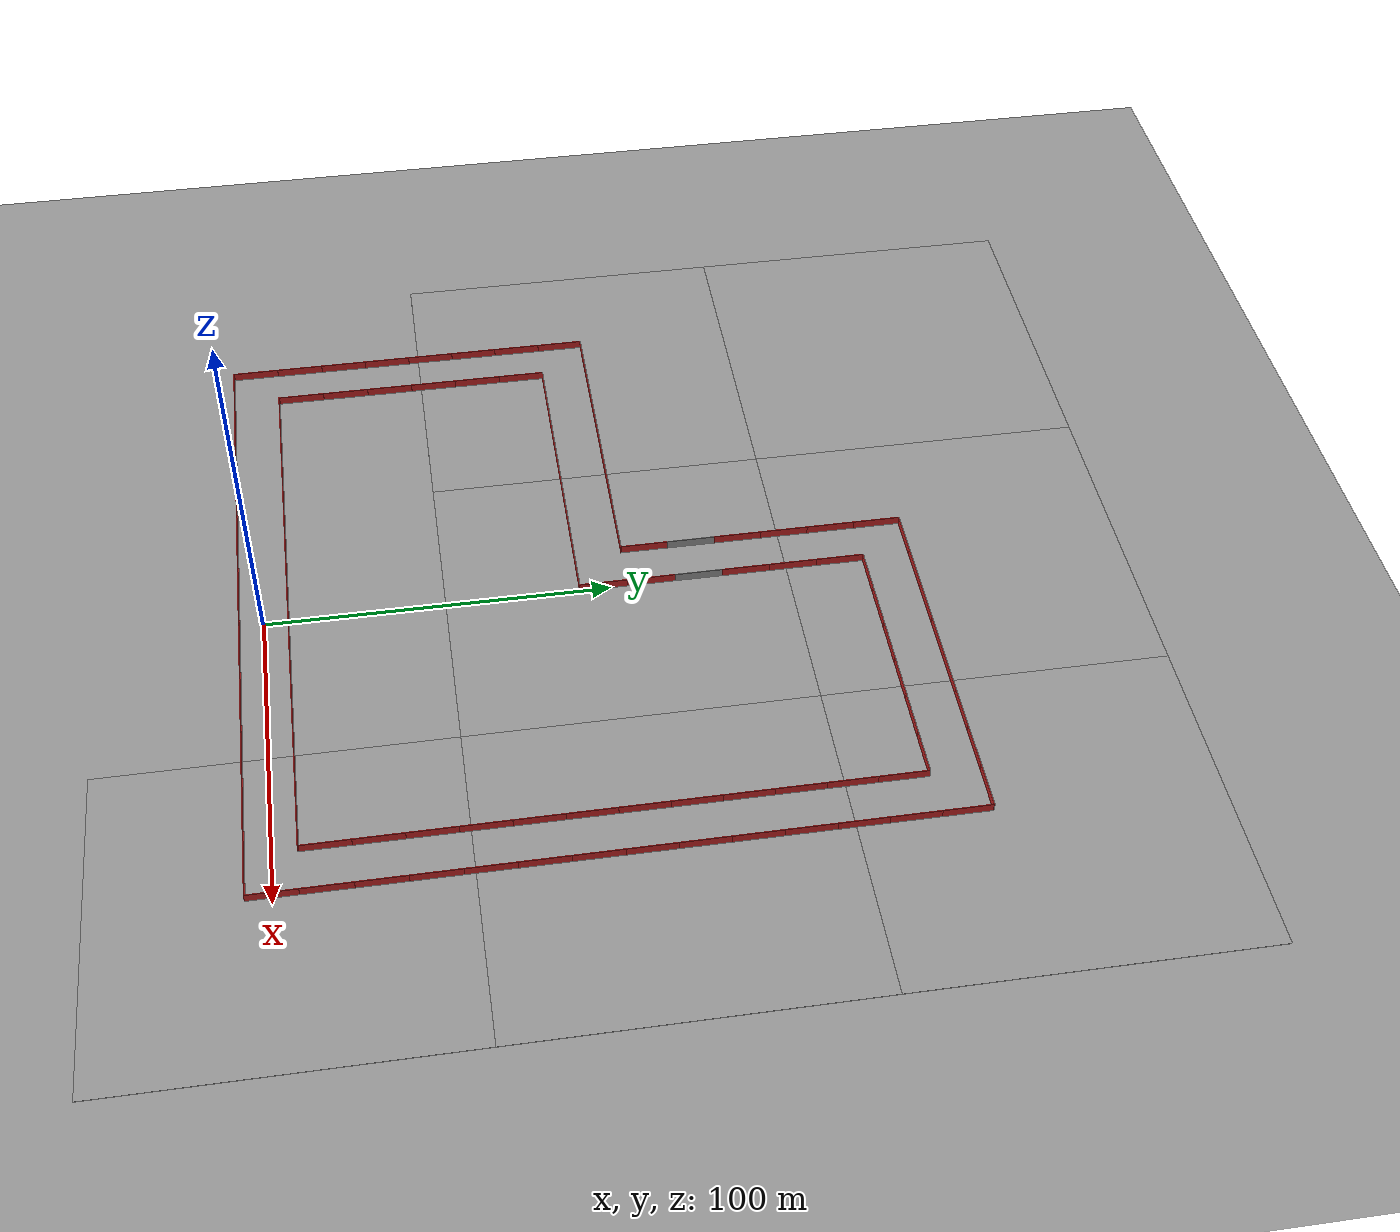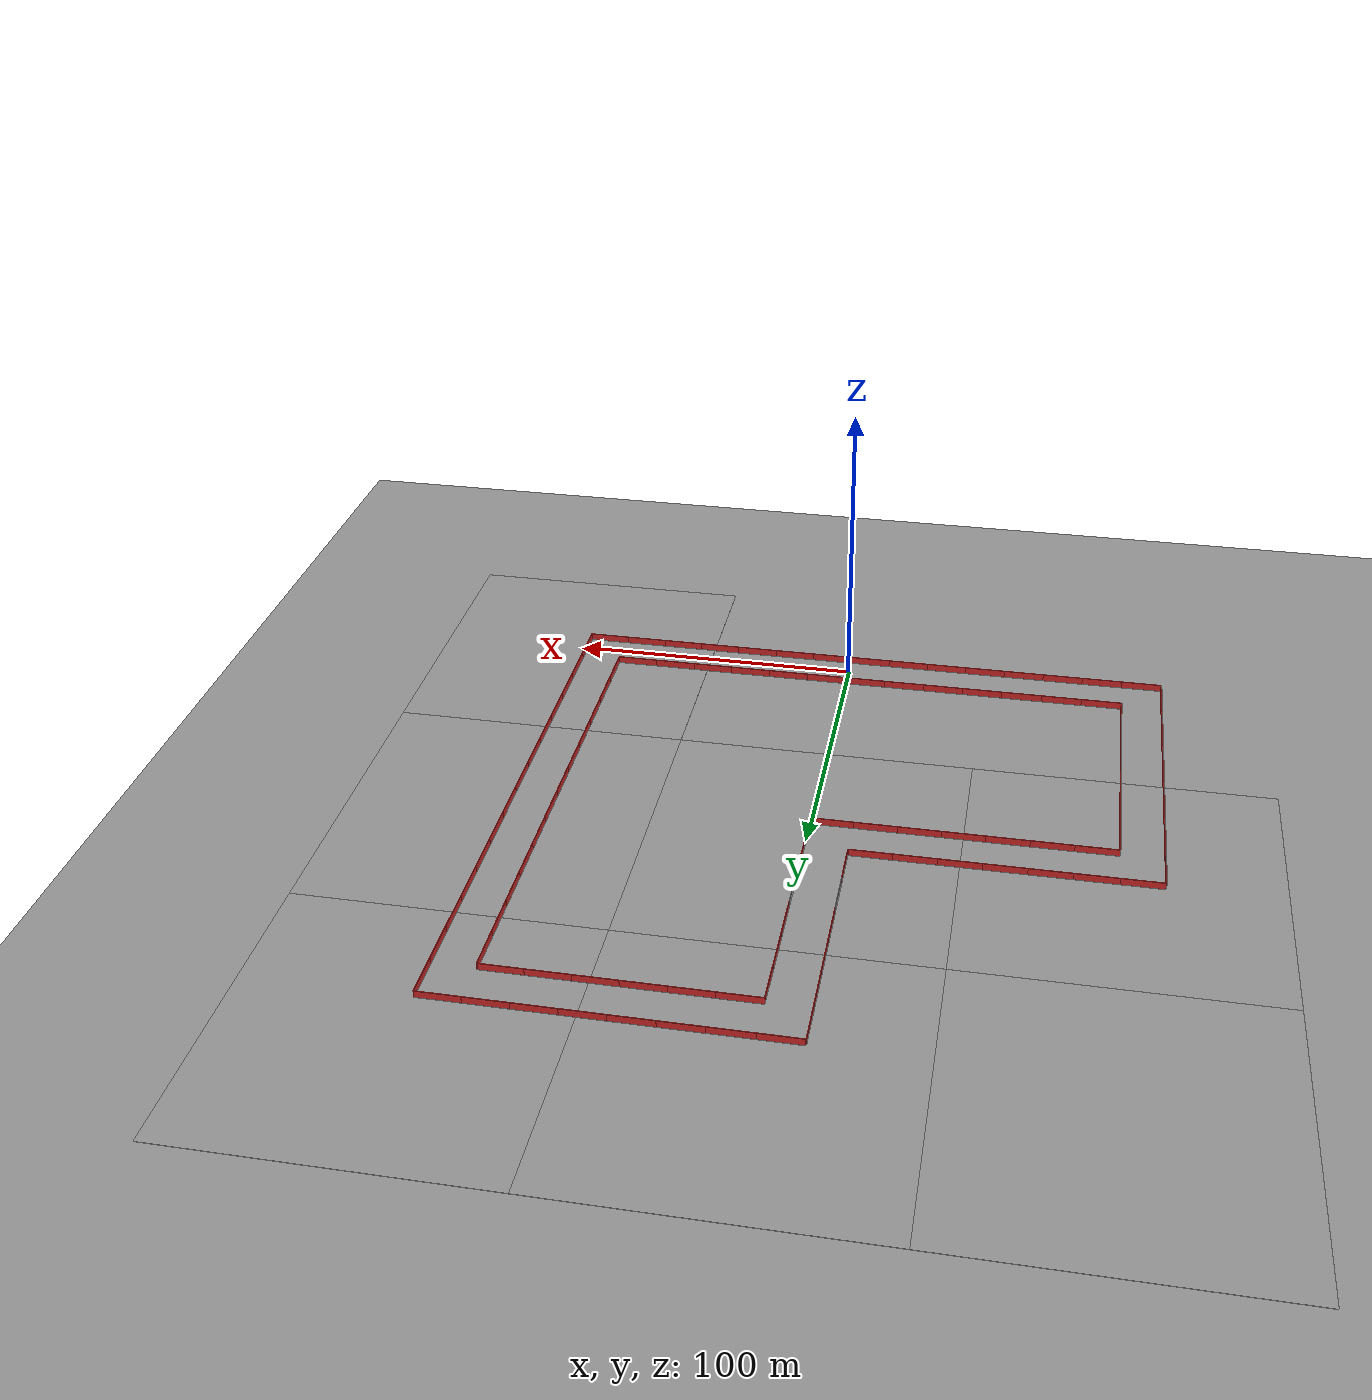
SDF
<sdf version="1.4">
 <world name="default">
  <light name="sun" type="directional">
   <pose>0 0 10 0 -0 0</pose>
   <diffuse>0.8 0.8 0.8 1</diffuse>
   <specular>0.2 0.2 0.2 1</specular>
   <attenuation>
    <range>1000</range>
    <constant>0.9</constant>
    <linear>0.01</linear>
    <quadratic>0.001</quadratic>
   </attenuation>
   <direction>-0.5 0.1 -0.9</direction>
  </light>
  <physics type="ode">
   <max_step_size>0.0025</max_step_size>
   <real_time_factor>1</real_time_factor>
   <real_time_update_rate>400</real_time_update_rate>
   <gravity>0 0 -9.8</gravity>
  </physics>
  <scene><ambient>0.4 0.4 0.4 1</ambient><background>0.7 0.7 0.7 1</background><shadows>0</shadows></scene>
  <spherical_coordinates>
   <surface_model>EARTH_WGS84</surface_model>
   <latitude_deg>0</latitude_deg>
   <longitude_deg>0</longitude_deg>
   <elevation>0</elevation>
   <heading_deg>0</heading_deg>
  </spherical_coordinates>
  <model name="staright_14m">
   <link name="Wall_26">
    <collision name="Wall_26_Collision">
     <geometry><box><size>14 0.2 2.5</size></box></geometry>
     <pose>0 0 1.25 0 -0 0</pose>
    </collision>
    <visual name="Wall_26_Visual">
     <pose>0 0 1.25 0 -0 0</pose>
     <geometry><box><size>14 0.2 2.5</size></box></geometry>
     <material>
      <script>
       <uri>model://materials/scripts</uri>
       <uri>model://materials/textures</uri>
       <name>vrc/red_wall</name>
      </script>
     </material>
    </visual>
    <velocity_decay><linear>0</linear><angular>0</angular></velocity_decay>
    <pose>0 -7 0 0 -0 0</pose>
   </link>
   <link name="Wall_28">
    <collision name="Wall_28_Collision">
     <geometry><box><size>14 0.2 2.5</size></box></geometry>
     <pose>0 0 1.25 0 -0 0</pose>
    </collision>
    <visual name="Wall_28_Visual">
     <pose>0 0 1.25 0 -0 0</pose>
     <geometry><box><size>14 0.2 2.5</size></box></geometry>
     <material>
      <script>
       <uri>model://materials/scripts</uri>
       <uri>model://materials/textures</uri>
       <name>vrc/red_wall</name>
      </script>
     </material>
    </visual>
    <velocity_decay><linear>0</linear><angular>0</angular></velocity_decay>
    <pose>0 7 0 0 -0 0</pose>
   </link>
   <static>1</static>
   <pose>7 0 0 0 -0 0</pose>
  </model>
  <model name="staright_28m_3">
   <link name="Wall_26">
    <collision name="Wall_26_Collision">
     <geometry><box><size>14 0.2 2.5</size></box></geometry>
     <pose>0 0 1.25 0 -0 0</pose>
    </collision>
    <visual name="Wall_26_Visual">
     <pose>0 0 1.25 0 -0 0</pose>
     <geometry><box><size>14 0.2 2.5</size></box></geometry>
     <material>
      <script>
       <uri>model://materials/scripts</uri>
       <uri>model://materials/textures</uri>
       <name>vrc/red_wall</name>
      </script>
     </material>
    </visual>
    <velocity_decay><linear>0</linear><angular>0</angular></velocity_decay>
    <pose>-7 -7 0 0 -0 0</pose>
   </link>
   <link name="Wall_28">
    <collision name="Wall_28_Collision">
     <geometry><box><size>14 0.2 2.5</size></box></geometry>
     <pose>0 0 1.25 0 -0 0</pose>
    </collision>
    <visual name="Wall_28_Visual">
     <pose>0 0 1.25 0 -0 0</pose>
     <geometry><box><size>14 0.2 2.5</size></box></geometry>
     <material>
      <script>
       <uri>model://materials/scripts</uri>
       <uri>model://materials/textures</uri>
       <name>vrc/red_wall</name>
      </script>
     </material>
    </visual>
    <velocity_decay><linear>0</linear><angular>0</angular></velocity_decay>
    <pose>-7 7 0 0 -0 0</pose>
   </link>
   <static>1</static>
   <link name="Wall_27">
    <collision name="Wall_26_Collision">
     <geometry><box><size>14 0.2 2.5</size></box></geometry>
     <pose>0 0 1.25 0 -0 0</pose>
    </collision>
    <visual name="Wall_26_Visual">
     <pose>0 0 1.25 0 -0 0</pose>
     <geometry><box><size>14 0.2 2.5</size></box></geometry>
     <material>
      <script>
       <uri>model://materials/scripts</uri>
       <uri>model://materials/textures</uri>
       <name>vrc/red_wall</name>
      </script>
     </material>
    </visual>
    <velocity_decay><linear>0</linear><angular>0</angular></velocity_decay>
    <pose>7 -7 0 0 -0 0</pose>
   </link>
   <link name="Wall_29">
    <collision name="Wall_28_Collision">
     <geometry><box><size>14 0.2 2.5</size></box></geometry>
     <pose>0 0 1.25 0 -0 0</pose>
    </collision>
    <visual name="Wall_28_Visual">
     <pose>0 0 1.25 0 -0 0</pose>
     <geometry><box><size>14 0.2 2.5</size></box></geometry>
     <material>
      <script>
       <uri>model://materials/scripts</uri>
       <uri>model://materials/textures</uri>
       <name>vrc/red_wall</name>
      </script>
     </material>
    </visual>
    <velocity_decay><linear>0</linear><angular>0</angular></velocity_decay>
    <pose>7 7 0 0 -0 0</pose>
   </link>
   <static>1</static>
   <pose>91 35 0 0 0 -1.5708</pose>
  </model>
  <model name="right_angle_turn_0">
   <link name="Wall_0">
    <collision name="Wall_0_Collision">
     <geometry><box><size>14.1 0.2 2.5</size></box></geometry>
     <pose>0 0 1.25 0 -0 0</pose>
    </collision>
    <visual name="Wall_0_Visual">
     <pose>0 0 1.25 0 -0 0</pose>
     <geometry><box><size>14.1 0.2 2.5</size></box></geometry>
     <material>
      <script>
       <uri>model://materials/scripts</uri>
       <uri>model://materials/textures</uri>
       <name>vrc/red_wall_x4</name>
      </script>
     </material>
    </visual>
    <velocity_decay><linear>0</linear><angular>0</angular></velocity_decay>
    <pose>0 -6.95 0 0 0 -1.5708</pose>
   </link>
   <link name="Wall_10">
    <collision name="Wall_10_Collision">
     <geometry><box><size>13.8 0.2 2.5</size></box></geometry>
     <pose>0 0 1.25 0 -0 0</pose>
    </collision>
    <visual name="Wall_10_Visual">
     <pose>0 0 1.25 0 -0 0</pose>
     <geometry><box><size>13.8 0.2 2.5</size></box></geometry>
     <material>
      <script>
       <uri>model://materials/scripts</uri>
       <uri>model://materials/textures</uri>
       <name>vrc/red_wall_x4</name>
      </script>
     </material>
    </visual>
    <velocity_decay><linear>0</linear><angular>0</angular></velocity_decay>
    <pose>14 7 0 0 0 -1.5708</pose>
   </link>
   <link name="Wall_2">
    <collision name="Wall_2_Collision">
     <geometry><box><size>13.9 0.2 2.5</size></box></geometry>
     <pose>0 0 1.25 0 -0 0</pose>
    </collision>
    <visual name="Wall_2_Visual">
     <pose>0 0 1.25 0 -0 0</pose>
     <geometry><box><size>13.9 0.2 2.5</size></box></geometry>
     <material>
      <script>
       <uri>model://materials/scripts</uri>
       <uri>model://materials/textures</uri>
       <name>vrc/red_wall_x4</name>
      </script>
     </material>
    </visual>
    <velocity_decay><linear>0</linear><angular>0</angular></velocity_decay>
    <pose>-7.05 0 0 0 -0 3.14159</pose>
   </link>
   <link name="Wall_4">
    <collision name="Wall_4_Collision">
     <geometry><box><size>14.1 0.2 2.5</size></box></geometry>
     <pose>0 0 1.25 0 -0 0</pose>
    </collision>
    <visual name="Wall_4_Visual">
     <pose>0 0 1.25 0 -0 0</pose>
     <geometry><box><size>14.1 0.2 2.5</size></box></geometry>
     <material>
      <script>
       <uri>model://materials/scripts</uri>
       <uri>model://materials/textures</uri>
       <name>vrc/red_wall_x4</name>
      </script>
     </material>
    </visual>
    <velocity_decay><linear>0</linear><angular>0</angular></velocity_decay>
    <pose>14 -6.95 0 0 -0 1.5708</pose>
   </link>
   <link name="Wall_6">
    <collision name="Wall_6_Collision">
     <geometry><box><size>14.1 0.2 2.5</size></box></geometry>
     <pose>0 0 1.25 0 -0 0</pose>
    </collision>
    <visual name="Wall_6_Visual">
     <pose>0 0 1.25 0 -0 0</pose>
     <geometry><box><size>14.1 0.2 2.5</size></box></geometry>
     <material>
      <script>
       <uri>model://materials/scripts</uri>
       <uri>model://materials/textures</uri>
       <name>vrc/red_wall_x4</name>
      </script>
     </material>
    </visual>
    <velocity_decay><linear>0</linear><angular>0</angular></velocity_decay>
    <pose>-6.95 14 0 0 -0 0</pose>
   </link>
   <link name="Wall_8">
    <collision name="Wall_8_Collision">
     <geometry><box><size>14 0.2 2.5</size></box></geometry>
     <pose>0 0 1.25 0 -0 0</pose>
    </collision>
    <visual name="Wall_8_Visual">
     <pose>0 0 1.25 0 -0 0</pose>
     <geometry><box><size>14 0.2 2.5</size></box></geometry>
     <material>
      <script>
       <uri>model://materials/scripts</uri>
       <uri>model://materials/textures</uri>
       <name>vrc/red_wall_x4</name>
      </script>
     </material>
    </visual>
    <velocity_decay><linear>0</linear><angular>0</angular></velocity_decay>
    <pose>7.1 14 0 0 -0 0</pose>
   </link>
   <static>1</static>
   <pose>0 175 0 0 -0 1.57079</pose>
  </model>
  <model name="right_angle_turn_1">
   <link name="Wall_0">
    <collision name="Wall_0_Collision">
     <geometry><box><size>14.1 0.2 2.5</size></box></geometry>
     <pose>0 0 1.25 0 -0 0</pose>
    </collision>
    <visual name="Wall_0_Visual">
     <pose>0 0 1.25 0 -0 0</pose>
     <geometry><box><size>14.1 0.2 2.5</size></box></geometry>
     <material>
      <script>
       <uri>model://materials/scripts</uri>
       <uri>model://materials/textures</uri>
       <name>vrc/red_wall_x4</name>
      </script>
     </material>
    </visual>
    <velocity_decay><linear>0</linear><angular>0</angular></velocity_decay>
    <pose>0 -6.95 0 0 0 -1.5708</pose>
   </link>
   <link name="Wall_10">
    <collision name="Wall_10_Collision">
     <geometry><box><size>13.8 0.2 2.5</size></box></geometry>
     <pose>0 0 1.25 0 -0 0</pose>
    </collision>
    <visual name="Wall_10_Visual">
     <pose>0 0 1.25 0 -0 0</pose>
     <geometry><box><size>13.8 0.2 2.5</size></box></geometry>
     <material>
      <script>
       <uri>model://materials/scripts</uri>
       <uri>model://materials/textures</uri>
       <name>vrc/red_wall_x4</name>
      </script>
     </material>
    </visual>
    <velocity_decay><linear>0</linear><angular>0</angular></velocity_decay>
    <pose>14 7 0 0 0 -1.5708</pose>
   </link>
   <link name="Wall_2">
    <collision name="Wall_2_Collision">
     <geometry><box><size>13.9 0.2 2.5</size></box></geometry>
     <pose>0 0 1.25 0 -0 0</pose>
    </collision>
    <visual name="Wall_2_Visual">
     <pose>0 0 1.25 0 -0 0</pose>
     <geometry><box><size>13.9 0.2 2.5</size></box></geometry>
     <material>
      <script>
       <uri>model://materials/scripts</uri>
       <uri>model://materials/textures</uri>
       <name>vrc/red_wall_x4</name>
      </script>
     </material>
    </visual>
    <velocity_decay><linear>0</linear><angular>0</angular></velocity_decay>
    <pose>-7.05 0 0 0 -0 3.14159</pose>
   </link>
   <link name="Wall_4">
    <collision name="Wall_4_Collision">
     <geometry><box><size>14.1 0.2 2.5</size></box></geometry>
     <pose>0 0 1.25 0 -0 0</pose>
    </collision>
    <visual name="Wall_4_Visual">
     <pose>0 0 1.25 0 -0 0</pose>
     <geometry><box><size>14.1 0.2 2.5</size></box></geometry>
     <material>
      <script>
       <uri>model://materials/scripts</uri>
       <uri>model://materials/textures</uri>
       <name>vrc/red_wall_x4</name>
      </script>
     </material>
    </visual>
    <velocity_decay><linear>0</linear><angular>0</angular></velocity_decay>
    <pose>14 -6.95 0 0 -0 1.5708</pose>
   </link>
   <link name="Wall_6">
    <collision name="Wall_6_Collision">
     <geometry><box><size>14.1 0.2 2.5</size></box></geometry>
     <pose>0 0 1.25 0 -0 0</pose>
    </collision>
    <visual name="Wall_6_Visual">
     <pose>0 0 1.25 0 -0 0</pose>
     <geometry><box><size>14.1 0.2 2.5</size></box></geometry>
     <material>
      <script>
       <uri>model://materials/scripts</uri>
       <uri>model://materials/textures</uri>
       <name>vrc/red_wall_x4</name>
      </script>
     </material>
    </visual>
    <velocity_decay><linear>0</linear><angular>0</angular></velocity_decay>
    <pose>-6.95 14 0 0 -0 0</pose>
   </link>
   <link name="Wall_8">
    <collision name="Wall_8_Collision">
     <geometry><box><size>14 0.2 2.5</size></box></geometry>
     <pose>0 0 1.25 0 -0 0</pose>
    </collision>
    <visual name="Wall_8_Visual">
     <pose>0 0 1.25 0 -0 0</pose>
     <geometry><box><size>14 0.2 2.5</size></box></geometry>
     <material>
      <script>
       <uri>model://materials/scripts</uri>
       <uri>model://materials/textures</uri>
       <name>vrc/red_wall_x4</name>
      </script>
     </material>
    </visual>
    <velocity_decay><linear>0</linear><angular>0</angular></velocity_decay>
    <pose>7.1 14 0 0 -0 0</pose>
   </link>
   <static>1</static>
   <pose>84 175 0 0 -0 0</pose>
  </model>
  <model name="staright_28m">
   <link name="Wall_26">
    <collision name="Wall_26_Collision">
     <geometry><box><size>14 0.2 2.5</size></box></geometry>
     <pose>0 0 1.25 0 -0 0</pose>
    </collision>
    <visual name="Wall_26_Visual">
     <pose>0 0 1.25 0 -0 0</pose>
     <geometry><box><size>14 0.2 2.5</size></box></geometry>
     <material>
      <script>
       <uri>model://materials/scripts</uri>
       <uri>model://materials/textures</uri>
       <name>vrc/red_wall</name>
      </script>
     </material>
    </visual>
    <velocity_decay><linear>0</linear><angular>0</angular></velocity_decay>
    <pose>-7 -7 0 0 -0 0</pose>
   </link>
   <link name="Wall_28">
    <collision name="Wall_28_Collision">
     <geometry><box><size>14 0.2 2.5</size></box></geometry>
     <pose>0 0 1.25 0 -0 0</pose>
    </collision>
    <visual name="Wall_28_Visual">
     <pose>0 0 1.25 0 -0 0</pose>
     <geometry><box><size>14 0.2 2.5</size></box></geometry>
     <material>
      <script>
       <uri>model://materials/scripts</uri>
       <uri>model://materials/textures</uri>
       <name>vrc/red_wall</name>
      </script>
     </material>
    </visual>
    <velocity_decay><linear>0</linear><angular>0</angular></velocity_decay>
    <pose>-7 7 0 0 -0 0</pose>
   </link>
   <static>1</static>
   <link name="Wall_27">
    <collision name="Wall_26_Collision">
     <geometry><box><size>14 0.2 2.5</size></box></geometry>
     <pose>0 0 1.25 0 -0 0</pose>
    </collision>
    <visual name="Wall_26_Visual">
     <pose>0 0 1.25 0 -0 0</pose>
     <geometry><box><size>14 0.2 2.5</size></box></geometry>
     <material>
      <script>
       <uri>model://materials/scripts</uri>
       <uri>model://materials/textures</uri>
       <name>vrc/red_wall</name>
      </script>
     </material>
    </visual>
    <velocity_decay><linear>0</linear><angular>0</angular></velocity_decay>
    <pose>7 -7 0 0 -0 0</pose>
   </link>
   <link name="Wall_29">
    <collision name="Wall_28_Collision">
     <geometry><box><size>14 0.2 2.5</size></box></geometry>
     <pose>0 0 1.25 0 -0 0</pose>
    </collision>
    <visual name="Wall_28_Visual">
     <pose>0 0 1.25 0 -0 0</pose>
     <geometry><box><size>14 0.2 2.5</size></box></geometry>
     <material>
      <script>
       <uri>model://materials/scripts</uri>
       <uri>model://materials/textures</uri>
       <name>vrc/red_wall</name>
      </script>
     </material>
    </visual>
    <velocity_decay><linear>0</linear><angular>0</angular></velocity_decay>
    <pose>7 7 0 0 -0 0</pose>
   </link>
   <static>1</static>
   <pose>28 0 0 0 -0 0</pose>
  </model>
  <model name="staright_28m_0">
   <link name="Wall_26">
    <collision name="Wall_26_Collision">
     <geometry><box><size>14 0.2 2.5</size></box></geometry>
     <pose>0 0 1.25 0 -0 0</pose>
    </collision>
    <visual name="Wall_26_Visual">
     <pose>0 0 1.25 0 -0 0</pose>
     <geometry><box><size>14 0.2 2.5</size></box></geometry>
     <material>
      <script>
       <uri>model://materials/scripts</uri>
       <uri>model://materials/textures</uri>
       <name>vrc/red_wall</name>
      </script>
     </material>
    </visual>
    <velocity_decay><linear>0</linear><angular>0</angular></velocity_decay>
    <pose>-7 -7 0 0 -0 0</pose>
   </link>
   <link name="Wall_28">
    <collision name="Wall_28_Collision">
     <geometry><box><size>14 0.2 2.5</size></box></geometry>
     <pose>0 0 1.25 0 -0 0</pose>
    </collision>
    <visual name="Wall_28_Visual">
     <pose>0 0 1.25 0 -0 0</pose>
     <geometry><box><size>14 0.2 2.5</size></box></geometry>
     <material>
      <script>
       <uri>model://materials/scripts</uri>
       <uri>model://materials/textures</uri>
       <name>vrc/red_wall</name>
      </script>
     </material>
    </visual>
    <velocity_decay><linear>0</linear><angular>0</angular></velocity_decay>
    <pose>-7 7 0 0 -0 0</pose>
   </link>
   <static>1</static>
   <link name="Wall_27">
    <collision name="Wall_26_Collision">
     <geometry><box><size>14 0.2 2.5</size></box></geometry>
     <pose>0 0 1.25 0 -0 0</pose>
    </collision>
    <visual name="Wall_26_Visual">
     <pose>0 0 1.25 0 -0 0</pose>
     <geometry><box><size>14 0.2 2.5</size></box></geometry>
     <material>
      <script>
       <uri>model://materials/scripts</uri>
       <uri>model://materials/textures</uri>
       <name>vrc/red_wall</name>
      </script>
     </material>
    </visual>
    <velocity_decay><linear>0</linear><angular>0</angular></velocity_decay>
    <pose>7 -7 0 0 -0 0</pose>
   </link>
   <link name="Wall_29">
    <collision name="Wall_28_Collision">
     <geometry><box><size>14 0.2 2.5</size></box></geometry>
     <pose>0 0 1.25 0 -0 0</pose>
    </collision>
    <visual name="Wall_28_Visual">
     <pose>0 0 1.25 0 -0 0</pose>
     <geometry><box><size>14 0.2 2.5</size></box></geometry>
     <material>
      <script>
       <uri>model://materials/scripts</uri>
       <uri>model://materials/textures</uri>
       <name>vrc/red_wall</name>
      </script>
     </material>
    </visual>
    <velocity_decay><linear>0</linear><angular>0</angular></velocity_decay>
    <pose>7 7 0 0 -0 0</pose>
   </link>
   <static>1</static>
   <pose>56 0 0 0 -0 0</pose>
  </model>
  <model name="right_angle_turn_2">
   <link name="Wall_0">
    <collision name="Wall_0_Collision">
     <geometry><box><size>14.1 0.2 2.5</size></box></geometry>
     <pose>0 0 1.25 0 -0 0</pose>
    </collision>
    <visual name="Wall_0_Visual">
     <pose>0 0 1.25 0 -0 0</pose>
     <geometry><box><size>14.1 0.2 2.5</size></box></geometry>
     <material>
      <script>
       <uri>model://materials/scripts</uri>
       <uri>model://materials/textures</uri>
       <name>vrc/red_wall_x4</name>
      </script>
     </material>
    </visual>
    <velocity_decay><linear>0</linear><angular>0</angular></velocity_decay>
    <pose>0 -6.95 0 0 0 -1.5708</pose>
   </link>
   <link name="Wall_10">
    <collision name="Wall_10_Collision">
     <geometry><box><size>13.8 0.2 2.5</size></box></geometry>
     <pose>0 0 1.25 0 -0 0</pose>
    </collision>
    <visual name="Wall_10_Visual">
     <pose>0 0 1.25 0 -0 0</pose>
     <geometry><box><size>13.8 0.2 2.5</size></box></geometry>
     <material>
      <script>
       <uri>model://materials/scripts</uri>
       <uri>model://materials/textures</uri>
       <name>vrc/red_wall_x4</name>
      </script>
     </material>
    </visual>
    <velocity_decay><linear>0</linear><angular>0</angular></velocity_decay>
    <pose>14 7 0 0 0 -1.5708</pose>
   </link>
   <link name="Wall_2">
    <collision name="Wall_2_Collision">
     <geometry><box><size>13.9 0.2 2.5</size></box></geometry>
     <pose>0 0 1.25 0 -0 0</pose>
    </collision>
    <visual name="Wall_2_Visual">
     <pose>0 0 1.25 0 -0 0</pose>
     <geometry><box><size>13.9 0.2 2.5</size></box></geometry>
     <material>
      <script>
       <uri>model://materials/scripts</uri>
       <uri>model://materials/textures</uri>
       <name>vrc/red_wall_x4</name>
      </script>
     </material>
    </visual>
    <velocity_decay><linear>0</linear><angular>0</angular></velocity_decay>
    <pose>-7.05 0 0 0 -0 3.14159</pose>
   </link>
   <link name="Wall_4">
    <collision name="Wall_4_Collision">
     <geometry><box><size>14.1 0.2 2.5</size></box></geometry>
     <pose>0 0 1.25 0 -0 0</pose>
    </collision>
    <visual name="Wall_4_Visual">
     <pose>0 0 1.25 0 -0 0</pose>
     <geometry><box><size>14.1 0.2 2.5</size></box></geometry>
     <material>
      <script>
       <uri>model://materials/scripts</uri>
       <uri>model://materials/textures</uri>
       <name>vrc/red_wall_x4</name>
      </script>
     </material>
    </visual>
    <velocity_decay><linear>0</linear><angular>0</angular></velocity_decay>
    <pose>14 -6.95 0 0 -0 1.5708</pose>
   </link>
   <link name="Wall_6">
    <collision name="Wall_6_Collision">
     <geometry><box><size>14.1 0.2 2.5</size></box></geometry>
     <pose>0 0 1.25 0 -0 0</pose>
    </collision>
    <visual name="Wall_6_Visual">
     <pose>0 0 1.25 0 -0 0</pose>
     <geometry><box><size>14.1 0.2 2.5</size></box></geometry>
     <material>
      <script>
       <uri>model://materials/scripts</uri>
       <uri>model://materials/textures</uri>
       <name>vrc/red_wall_x4</name>
      </script>
     </material>
    </visual>
    <velocity_decay><linear>0</linear><angular>0</angular></velocity_decay>
    <pose>-6.95 14 0 0 -0 0</pose>
   </link>
   <link name="Wall_8">
    <collision name="Wall_8_Collision">
     <geometry><box><size>14 0.2 2.5</size></box></geometry>
     <pose>0 0 1.25 0 -0 0</pose>
    </collision>
    <visual name="Wall_8_Visual">
     <pose>0 0 1.25 0 -0 0</pose>
     <geometry><box><size>14 0.2 2.5</size></box></geometry>
     <material>
      <script>
       <uri>model://materials/scripts</uri>
       <uri>model://materials/textures</uri>
       <name>vrc/red_wall_x4</name>
      </script>
     </material>
    </visual>
    <velocity_decay><linear>0</linear><angular>0</angular></velocity_decay>
    <pose>7.1 14 0 0 -0 0</pose>
   </link>
   <static>1</static>
   <pose>84 7.00001 0 0 0 -1.57079</pose>
  </model>
  <model name="staright_28m_4">
   <link name="Wall_26">
    <collision name="Wall_26_Collision">
     <geometry><box><size>14 0.2 2.5</size></box></geometry>
     <pose>0 0 1.25 0 -0 0</pose>
    </collision>
    <visual name="Wall_26_Visual">
     <pose>0 0 1.25 0 -0 0</pose>
     <geometry><box><size>14 0.2 2.5</size></box></geometry>
     <material>
      <script>
       <uri>model://materials/scripts</uri>
       <uri>model://materials/textures</uri>
       <name>vrc/red_wall</name>
      </script>
     </material>
    </visual>
    <velocity_decay><linear>0</linear><angular>0</angular></velocity_decay>
    <pose>-7 -7 0 0 -0 0</pose>
   </link>
   <link name="Wall_28">
    <collision name="Wall_28_Collision">
     <geometry><box><size>14 0.2 2.5</size></box></geometry>
     <pose>0 0 1.25 0 -0 0</pose>
    </collision>
    <visual name="Wall_28_Visual">
     <pose>0 0 1.25 0 -0 0</pose>
     <geometry><box><size>14 0.2 2.5</size></box></geometry>
     <material>
      <script>
       <uri>model://materials/scripts</uri>
       <uri>model://materials/textures</uri>
       <name>vrc/red_wall</name>
      </script>
     </material>
    </visual>
    <velocity_decay><linear>0</linear><angular>0</angular></velocity_decay>
    <pose>-7 7 0 0 -0 0</pose>
   </link>
   <static>1</static>
   <link name="Wall_27">
    <collision name="Wall_26_Collision">
     <geometry><box><size>14 0.2 2.5</size></box></geometry>
     <pose>0 0 1.25 0 -0 0</pose>
    </collision>
    <visual name="Wall_26_Visual">
     <pose>0 0 1.25 0 -0 0</pose>
     <geometry><box><size>14 0.2 2.5</size></box></geometry>
     <material>
      <script>
       <uri>model://materials/scripts</uri>
       <uri>model://materials/textures</uri>
       <name>vrc/red_wall</name>
      </script>
     </material>
    </visual>
    <velocity_decay><linear>0</linear><angular>0</angular></velocity_decay>
    <pose>7 -7 0 0 -0 0</pose>
   </link>
   <link name="Wall_29">
    <collision name="Wall_28_Collision">
     <geometry><box><size>14 0.2 2.5</size></box></geometry>
     <pose>0 0 1.25 0 -0 0</pose>
    </collision>
    <visual name="Wall_28_Visual">
     <pose>0 0 1.25 0 -0 0</pose>
     <geometry><box><size>14 0.2 2.5</size></box></geometry>
     <material>
      <script>
       <uri>model://materials/scripts</uri>
       <uri>model://materials/textures</uri>
       <name>vrc/red_wall</name>
      </script>
     </material>
    </visual>
    <velocity_decay><linear>0</linear><angular>0</angular></velocity_decay>
    <pose>7 7 0 0 -0 0</pose>
   </link>
   <static>1</static>
   <pose>91 63 0 0 0 -1.5708</pose>
  </model>
  <model name="staright_28m_5">
   <link name="Wall_26">
    <collision name="Wall_26_Collision">
     <geometry><box><size>14 0.2 2.5</size></box></geometry>
     <pose>0 0 1.25 0 -0 0</pose>
    </collision>
    <visual name="Wall_26_Visual">
     <pose>0 0 1.25 0 -0 0</pose>
     <geometry><box><size>14 0.2 2.5</size></box></geometry>
     <material>
      <script>
       <uri>model://materials/scripts</uri>
       <uri>model://materials/textures</uri>
       <name>vrc/red_wall</name>
      </script>
     </material>
    </visual>
    <velocity_decay><linear>0</linear><angular>0</angular></velocity_decay>
    <pose>-7 -7 0 0 -0 0</pose>
   </link>
   <link name="Wall_28">
    <collision name="Wall_28_Collision">
     <geometry><box><size>14 0.2 2.5</size></box></geometry>
     <pose>0 0 1.25 0 -0 0</pose>
    </collision>
    <visual name="Wall_28_Visual">
     <pose>0 0 1.25 0 -0 0</pose>
     <geometry><box><size>14 0.2 2.5</size></box></geometry>
     <material>
      <script>
       <uri>model://materials/scripts</uri>
       <uri>model://materials/textures</uri>
       <name>vrc/red_wall</name>
      </script>
     </material>
    </visual>
    <velocity_decay><linear>0</linear><angular>0</angular></velocity_decay>
    <pose>-7 7 0 0 -0 0</pose>
   </link>
   <static>1</static>
   <link name="Wall_27">
    <collision name="Wall_26_Collision">
     <geometry><box><size>14 0.2 2.5</size></box></geometry>
     <pose>0 0 1.25 0 -0 0</pose>
    </collision>
    <visual name="Wall_26_Visual">
     <pose>0 0 1.25 0 -0 0</pose>
     <geometry><box><size>14 0.2 2.5</size></box></geometry>
     <material>
      <script>
       <uri>model://materials/scripts</uri>
       <uri>model://materials/textures</uri>
       <name>vrc/red_wall</name>
      </script>
     </material>
    </visual>
    <velocity_decay><linear>0</linear><angular>0</angular></velocity_decay>
    <pose>7 -7 0 0 -0 0</pose>
   </link>
   <link name="Wall_29">
    <collision name="Wall_28_Collision">
     <geometry><box><size>14 0.2 2.5</size></box></geometry>
     <pose>0 0 1.25 0 -0 0</pose>
    </collision>
    <visual name="Wall_28_Visual">
     <pose>0 0 1.25 0 -0 0</pose>
     <geometry><box><size>14 0.2 2.5</size></box></geometry>
     <material>
      <script>
       <uri>model://materials/scripts</uri>
       <uri>model://materials/textures</uri>
       <name>vrc/red_wall</name>
      </script>
     </material>
    </visual>
    <velocity_decay><linear>0</linear><angular>0</angular></velocity_decay>
    <pose>7 7 0 0 -0 0</pose>
   </link>
   <static>1</static>
   <pose>28 182 0 0 -0 0</pose>
  </model>
  <model name="staright_28m_6">
   <link name="Wall_26">
    <collision name="Wall_26_Collision">
     <geometry><box><size>14 0.2 2.5</size></box></geometry>
     <pose>0 0 1.25 0 -0 0</pose>
    </collision>
    <visual name="Wall_26_Visual">
     <pose>0 0 1.25 0 -0 0</pose>
     <geometry><box><size>14 0.2 2.5</size></box></geometry>
     <material>
      <script>
       <uri>model://materials/scripts</uri>
       <uri>model://materials/textures</uri>
       <name>vrc/red_wall</name>
      </script>
     </material>
    </visual>
    <velocity_decay><linear>0</linear><angular>0</angular></velocity_decay>
    <pose>-7 -7 0 0 -0 0</pose>
   </link>
   <link name="Wall_28">
    <collision name="Wall_28_Collision">
     <geometry><box><size>14 0.2 2.5</size></box></geometry>
     <pose>0 0 1.25 0 -0 0</pose>
    </collision>
    <visual name="Wall_28_Visual">
     <pose>0 0 1.25 0 -0 0</pose>
     <geometry><box><size>14 0.2 2.5</size></box></geometry>
     <material>
      <script>
       <uri>model://materials/scripts</uri>
       <uri>model://materials/textures</uri>
       <name>vrc/red_wall</name>
      </script>
     </material>
    </visual>
    <velocity_decay><linear>0</linear><angular>0</angular></velocity_decay>
    <pose>-7 7 0 0 -0 0</pose>
   </link>
   <static>1</static>
   <link name="Wall_27">
    <collision name="Wall_26_Collision">
     <geometry><box><size>14 0.2 2.5</size></box></geometry>
     <pose>0 0 1.25 0 -0 0</pose>
    </collision>
    <visual name="Wall_26_Visual">
     <pose>0 0 1.25 0 -0 0</pose>
     <geometry><box><size>14 0.2 2.5</size></box></geometry>
     <material>
      <script>
       <uri>model://materials/scripts</uri>
       <uri>model://materials/textures</uri>
       <name>vrc/red_wall</name>
      </script>
     </material>
    </visual>
    <velocity_decay><linear>0</linear><angular>0</angular></velocity_decay>
    <pose>7 -7 0 0 -0 0</pose>
   </link>
   <link name="Wall_29">
    <collision name="Wall_28_Collision">
     <geometry><box><size>14 0.2 2.5</size></box></geometry>
     <pose>0 0 1.25 0 -0 0</pose>
    </collision>
    <visual name="Wall_28_Visual">
     <pose>0 0 1.25 0 -0 0</pose>
     <geometry><box><size>14 0.2 2.5</size></box></geometry>
     <material>
      <script>
       <uri>model://materials/scripts</uri>
       <uri>model://materials/textures</uri>
       <name>vrc/red_wall</name>
      </script>
     </material>
    </visual>
    <velocity_decay><linear>0</linear><angular>0</angular></velocity_decay>
    <pose>7 7 0 0 -0 0</pose>
   </link>
   <static>1</static>
   <pose>56 182 0 0 -0 0</pose>
  </model>
  <model name="staright_28m_7">
   <link name="Wall_26">
    <collision name="Wall_26_Collision">
     <geometry><box><size>14 0.2 2.5</size></box></geometry>
     <pose>0 0 1.25 0 -0 0</pose>
    </collision>
    <visual name="Wall_26_Visual">
     <pose>0 0 1.25 0 -0 0</pose>
     <geometry><box><size>14 0.2 2.5</size></box></geometry>
     <material>
      <script>
       <uri>model://materials/scripts</uri>
       <uri>model://materials/textures</uri>
       <name>vrc/red_wall</name>
      </script>
     </material>
    </visual>
    <velocity_decay><linear>0</linear><angular>0</angular></velocity_decay>
    <pose>-7 -7 0 0 -0 0</pose>
   </link>
   <link name="Wall_28">
    <collision name="Wall_28_Collision">
     <geometry><box><size>14 0.2 2.5</size></box></geometry>
     <pose>0 0 1.25 0 -0 0</pose>
    </collision>
    <visual name="Wall_28_Visual">
     <pose>0 0 1.25 0 -0 0</pose>
     <geometry><box><size>14 0.2 2.5</size></box></geometry>
     <material>
      <script>
       <uri>model://materials/scripts</uri>
       <uri>model://materials/textures</uri>
       <name>vrc/red_wall</name>
      </script>
     </material>
    </visual>
    <velocity_decay><linear>0</linear><angular>0</angular></velocity_decay>
    <pose>-7 7 0 0 -0 0</pose>
   </link>
   <static>1</static>
   <link name="Wall_27">
    <collision name="Wall_26_Collision">
     <geometry><box><size>14 0.2 2.5</size></box></geometry>
     <pose>0 0 1.25 0 -0 0</pose>
    </collision>
    <visual name="Wall_26_Visual">
     <pose>0 0 1.25 0 -0 0</pose>
     <geometry><box><size>14 0.2 2.5</size></box></geometry>
     <material>
      <script>
       <uri>model://materials/scripts</uri>
       <uri>model://materials/textures</uri>
       <name>vrc/red_wall</name>
      </script>
     </material>
    </visual>
    <velocity_decay><linear>0</linear><angular>0</angular></velocity_decay>
    <pose>7 -7 0 0 -0 0</pose>
   </link>
   <link name="Wall_29">
    <collision name="Wall_28_Collision">
     <geometry><box><size>14 0.2 2.5</size></box></geometry>
     <pose>0 0 1.25 0 -0 0</pose>
    </collision>
    <visual name="Wall_28_Visual">
     <pose>0 0 1.25 0 -0 0</pose>
     <geometry><box><size>14 0.2 2.5</size></box></geometry>
     <material>
      <script>
       <uri>model://materials/scripts</uri>
       <uri>model://materials/textures</uri>
       <name>vrc/red_wall</name>
      </script>
     </material>
    </visual>
    <velocity_decay><linear>0</linear><angular>0</angular></velocity_decay>
    <pose>7 7 0 0 -0 0</pose>
   </link>
   <static>1</static>
   <pose>91 91 0 0 0 -1.5708</pose>
  </model>
  <model name="right_angle_turn">
   <link name="Wall_0">
    <collision name="Wall_0_Collision">
     <geometry><box><size>14.1 0.2 2.5</size></box></geometry>
     <pose>0 0 1.25 0 -0 0</pose>
    </collision>
    <visual name="Wall_0_Visual">
     <pose>0 0 1.25 0 -0 0</pose>
     <geometry><box><size>14.1 0.2 2.5</size></box></geometry>
     <material>
      <script>
       <uri>model://materials/scripts</uri>
       <uri>model://materials/textures</uri>
       <name>vrc/red_wall_x4</name>
      </script>
     </material>
    </visual>
    <velocity_decay><linear>0</linear><angular>0</angular></velocity_decay>
    <pose>0 -6.95 0 0 0 -1.5708</pose>
   </link>
   <link name="Wall_10">
    <collision name="Wall_10_Collision">
     <geometry><box><size>13.8 0.2 2.5</size></box></geometry>
     <pose>0 0 1.25 0 -0 0</pose>
    </collision>
    <visual name="Wall_10_Visual">
     <pose>0 0 1.25 0 -0 0</pose>
     <geometry><box><size>13.8 0.2 2.5</size></box></geometry>
     <material>
      <script>
       <uri>model://materials/scripts</uri>
       <uri>model://materials/textures</uri>
       <name>vrc/red_wall_x4</name>
      </script>
     </material>
    </visual>
    <velocity_decay><linear>0</linear><angular>0</angular></velocity_decay>
    <pose>14 7 0 0 0 -1.5708</pose>
   </link>
   <link name="Wall_2">
    <collision name="Wall_2_Collision">
     <geometry><box><size>13.9 0.2 2.5</size></box></geometry>
     <pose>0 0 1.25 0 -0 0</pose>
    </collision>
    <visual name="Wall_2_Visual">
     <pose>0 0 1.25 0 -0 0</pose>
     <geometry><box><size>13.9 0.2 2.5</size></box></geometry>
     <material>
      <script>
       <uri>model://materials/scripts</uri>
       <uri>model://materials/textures</uri>
       <name>vrc/red_wall_x4</name>
      </script>
     </material>
    </visual>
    <velocity_decay><linear>0</linear><angular>0</angular></velocity_decay>
    <pose>-7.05 0 0 0 -0 3.14159</pose>
   </link>
   <link name="Wall_4">
    <collision name="Wall_4_Collision">
     <geometry><box><size>14.1 0.2 2.5</size></box></geometry>
     <pose>0 0 1.25 0 -0 0</pose>
    </collision>
    <visual name="Wall_4_Visual">
     <pose>0 0 1.25 0 -0 0</pose>
     <geometry><box><size>14.1 0.2 2.5</size></box></geometry>
     <material>
      <script>
       <uri>model://materials/scripts</uri>
       <uri>model://materials/textures</uri>
       <name>vrc/red_wall_x4</name>
      </script>
     </material>
    </visual>
    <velocity_decay><linear>0</linear><angular>0</angular></velocity_decay>
    <pose>14 -6.95 0 0 -0 1.5708</pose>
   </link>
   <link name="Wall_6">
    <collision name="Wall_6_Collision">
     <geometry><box><size>14.1 0.2 2.5</size></box></geometry>
     <pose>0 0 1.25 0 -0 0</pose>
    </collision>
    <visual name="Wall_6_Visual">
     <pose>0 0 1.25 0 -0 0</pose>
     <geometry><box><size>14.1 0.2 2.5</size></box></geometry>
     <material>
      <script>
       <uri>model://materials/scripts</uri>
       <uri>model://materials/textures</uri>
       <name>vrc/red_wall_x4</name>
      </script>
     </material>
    </visual>
    <velocity_decay><linear>0</linear><angular>0</angular></velocity_decay>
    <pose>-6.95 14 0 0 -0 0</pose>
   </link>
   <link name="Wall_8">
    <collision name="Wall_8_Collision">
     <geometry><box><size>14 0.2 2.5</size></box></geometry>
     <pose>0 0 1.25 0 -0 0</pose>
    </collision>
    <visual name="Wall_8_Visual">
     <pose>0 0 1.25 0 -0 0</pose>
     <geometry><box><size>14 0.2 2.5</size></box></geometry>
     <material>
      <script>
       <uri>model://materials/scripts</uri>
       <uri>model://materials/textures</uri>
       <name>vrc/red_wall_x4</name>
      </script>
     </material>
    </visual>
    <velocity_decay><linear>0</linear><angular>0</angular></velocity_decay>
    <pose>7.1 14 0 0 -0 0</pose>
   </link>
   <static>1</static>
   <pose>-14 105 0 0 0 -1.57079</pose>
  </model>
  <model name="staright_28m_8">
   <link name="Wall_26">
    <collision name="Wall_26_Collision">
     <geometry><box><size>14 0.2 2.5</size></box></geometry>
     <pose>0 0 1.25 0 -0 0</pose>
    </collision>
    <visual name="Wall_26_Visual">
     <pose>0 0 1.25 0 -0 0</pose>
     <geometry><box><size>14 0.2 2.5</size></box></geometry>
     <material>
      <script>
       <uri>model://materials/scripts</uri>
       <uri>model://materials/textures</uri>
       <name>vrc/red_wall</name>
      </script>
     </material>
    </visual>
    <velocity_decay><linear>0</linear><angular>0</angular></velocity_decay>
    <pose>-7 -7 0 0 -0 0</pose>
   </link>
   <link name="Wall_28">
    <collision name="Wall_28_Collision">
     <geometry><box><size>14 0.2 2.5</size></box></geometry>
     <pose>0 0 1.25 0 -0 0</pose>
    </collision>
    <visual name="Wall_28_Visual">
     <pose>0 0 1.25 0 -0 0</pose>
     <geometry><box><size>14 0.2 2.5</size></box></geometry>
     <material>
      <script>
       <uri>model://materials/scripts</uri>
       <uri>model://materials/textures</uri>
       <name>vrc/red_wall</name>
      </script>
     </material>
    </visual>
    <velocity_decay><linear>0</linear><angular>0</angular></velocity_decay>
    <pose>-7 7 0 0 -0 0</pose>
   </link>
   <static>1</static>
   <link name="Wall_27">
    <collision name="Wall_26_Collision">
     <geometry><box><size>14 0.2 2.5</size></box></geometry>
     <pose>0 0 1.25 0 -0 0</pose>
    </collision>
    <visual name="Wall_26_Visual">
     <pose>0 0 1.25 0 -0 0</pose>
     <geometry><box><size>14 0.2 2.5</size></box></geometry>
     <material>
      <script>
       <uri>model://materials/scripts</uri>
       <uri>model://materials/textures</uri>
       <name>vrc/red_wall</name>
      </script>
     </material>
    </visual>
    <velocity_decay><linear>0</linear><angular>0</angular></velocity_decay>
    <pose>7 -7 0 0 -0 0</pose>
   </link>
   <link name="Wall_29">
    <collision name="Wall_28_Collision">
     <geometry><box><size>14 0.2 2.5</size></box></geometry>
     <pose>0 0 1.25 0 -0 0</pose>
    </collision>
    <visual name="Wall_28_Visual">
     <pose>0 0 1.25 0 -0 0</pose>
     <geometry><box><size>14 0.2 2.5</size></box></geometry>
     <material>
      <script>
       <uri>model://materials/scripts</uri>
       <uri>model://materials/textures</uri>
       <name>vrc/red_wall</name>
      </script>
     </material>
    </visual>
    <velocity_decay><linear>0</linear><angular>0</angular></velocity_decay>
    <pose>7 7 0 0 -0 0</pose>
   </link>
   <static>1</static>
   <pose>91 119 0 0 0 -1.5708</pose>
  </model>
  <model name="staright_28m_9">
   <link name="Wall_26">
    <collision name="Wall_26_Collision">
     <geometry><box><size>14 0.2 2.5</size></box></geometry>
     <pose>0 0 1.25 0 -0 0</pose>
    </collision>
    <visual name="Wall_26_Visual">
     <pose>0 0 1.25 0 -0 0</pose>
     <geometry><box><size>14 0.2 2.5</size></box></geometry>
     <material>
      <script>
       <uri>model://materials/scripts</uri>
       <uri>model://materials/textures</uri>
       <name>vrc/red_wall</name>
      </script>
     </material>
    </visual>
    <velocity_decay><linear>0</linear><angular>0</angular></velocity_decay>
    <pose>-7 -7 0 0 -0 0</pose>
   </link>
   <link name="Wall_28">
    <collision name="Wall_28_Collision">
     <geometry><box><size>14 0.2 2.5</size></box></geometry>
     <pose>0 0 1.25 0 -0 0</pose>
    </collision>
    <visual name="Wall_28_Visual">
     <pose>0 0 1.25 0 -0 0</pose>
     <geometry><box><size>14 0.2 2.5</size></box></geometry>
     <material>
      <script>
       <uri>model://materials/scripts</uri>
       <uri>model://materials/textures</uri>
       <name>vrc/red_wall</name>
      </script>
     </material>
    </visual>
    <velocity_decay><linear>0</linear><angular>0</angular></velocity_decay>
    <pose>-7 7 0 0 -0 0</pose>
   </link>
   <static>1</static>
   <link name="Wall_27">
    <collision name="Wall_26_Collision">
     <geometry><box><size>14 0.2 2.5</size></box></geometry>
     <pose>0 0 1.25 0 -0 0</pose>
    </collision>
    <visual name="Wall_26_Visual">
     <pose>0 0 1.25 0 -0 0</pose>
     <geometry><box><size>14 0.2 2.5</size></box></geometry>
     <material>
      <script>
       <uri>model://materials/scripts</uri>
       <uri>model://materials/textures</uri>
       <name>vrc/red_wall</name>
      </script>
     </material>
    </visual>
    <velocity_decay><linear>0</linear><angular>0</angular></velocity_decay>
    <pose>7 -7 0 0 -0 0</pose>
   </link>
   <link name="Wall_29">
    <collision name="Wall_28_Collision">
     <geometry><box><size>14 0.2 2.5</size></box></geometry>
     <pose>0 0 1.25 0 -0 0</pose>
    </collision>
    <visual name="Wall_28_Visual">
     <pose>0 0 1.25 0 -0 0</pose>
     <geometry><box><size>14 0.2 2.5</size></box></geometry>
     <material>
      <script>
       <uri>model://materials/scripts</uri>
       <uri>model://materials/textures</uri>
       <name>vrc/red_wall</name>
      </script>
     </material>
    </visual>
    <velocity_decay><linear>0</linear><angular>0</angular></velocity_decay>
    <pose>7 7 0 0 -0 0</pose>
   </link>
   <static>1</static>
   <pose>-42 98 0 0 -0 0</pose>
  </model>
  <model name="staright_28m_10">
   <link name="Wall_26">
    <collision name="Wall_26_Collision">
     <geometry><box><size>14 0.2 2.5</size></box></geometry>
     <pose>0 0 1.25 0 -0 0</pose>
    </collision>
    <visual name="Wall_26_Visual">
     <pose>0 0 1.25 0 -0 0</pose>
     <geometry><box><size>14 0.2 2.5</size></box></geometry>
     <material>
      <script>
       <uri>model://materials/scripts</uri>
       <uri>model://materials/textures</uri>
       <name>vrc/red_wall</name>
      </script>
     </material>
    </visual>
    <velocity_decay><linear>0</linear><angular>0</angular></velocity_decay>
    <pose>-7 -7 0 0 -0 0</pose>
   </link>
   <link name="Wall_28">
    <collision name="Wall_28_Collision">
     <geometry><box><size>14 0.2 2.5</size></box></geometry>
     <pose>0 0 1.25 0 -0 0</pose>
    </collision>
    <visual name="Wall_28_Visual">
     <pose>0 0 1.25 0 -0 0</pose>
     <geometry><box><size>14 0.2 2.5</size></box></geometry>
     <material>
      <script>
       <uri>model://materials/scripts</uri>
       <uri>model://materials/textures</uri>
       <name>vrc/red_wall</name>
      </script>
     </material>
    </visual>
    <velocity_decay><linear>0</linear><angular>0</angular></velocity_decay>
    <pose>-7 7 0 0 -0 0</pose>
   </link>
   <static>1</static>
   <link name="Wall_27">
    <collision name="Wall_26_Collision">
     <geometry><box><size>14 0.2 2.5</size></box></geometry>
     <pose>0 0 1.25 0 -0 0</pose>
    </collision>
    <visual name="Wall_26_Visual">
     <pose>0 0 1.25 0 -0 0</pose>
     <geometry><box><size>14 0.2 2.5</size></box></geometry>
     <material>
      <script>
       <uri>model://materials/scripts</uri>
       <uri>model://materials/textures</uri>
       <name>vrc/red_wall</name>
      </script>
     </material>
    </visual>
    <velocity_decay><linear>0</linear><angular>0</angular></velocity_decay>
    <pose>7 -7 0 0 -0 0</pose>
   </link>
   <link name="Wall_29">
    <collision name="Wall_28_Collision">
     <geometry><box><size>14 0.2 2.5</size></box></geometry>
     <pose>0 0 1.25 0 -0 0</pose>
    </collision>
    <visual name="Wall_28_Visual">
     <pose>0 0 1.25 0 -0 0</pose>
     <geometry><box><size>14 0.2 2.5</size></box></geometry>
     <material>
      <script>
       <uri>model://materials/scripts</uri>
       <uri>model://materials/textures</uri>
       <name>vrc/red_wall</name>
      </script>
     </material>
    </visual>
    <velocity_decay><linear>0</linear><angular>0</angular></velocity_decay>
    <pose>7 7 0 0 -0 0</pose>
   </link>
   <static>1</static>
   <pose>-70 98 0 0 -0 0</pose>
  </model>
  <model name="staright_28m_11">
   <link name="Wall_26">
    <collision name="Wall_26_Collision">
     <geometry><box><size>14 0.2 2.5</size></box></geometry>
     <pose>0 0 1.25 0 -0 0</pose>
    </collision>
    <visual name="Wall_26_Visual">
     <pose>0 0 1.25 0 -0 0</pose>
     <geometry><box><size>14 0.2 2.5</size></box></geometry>
     <material>
      <script>
       <uri>model://materials/scripts</uri>
       <uri>model://materials/textures</uri>
       <name>vrc/red_wall</name>
      </script>
     </material>
    </visual>
    <velocity_decay><linear>0</linear><angular>0</angular></velocity_decay>
    <pose>-7 -7 0 0 -0 0</pose>
   </link>
   <link name="Wall_28">
    <collision name="Wall_28_Collision">
     <geometry><box><size>14 0.2 2.5</size></box></geometry>
     <pose>0 0 1.25 0 -0 0</pose>
    </collision>
    <visual name="Wall_28_Visual">
     <pose>0 0 1.25 0 -0 0</pose>
     <geometry><box><size>14 0.2 2.5</size></box></geometry>
     <material>
      <script>
       <uri>model://materials/scripts</uri>
       <uri>model://materials/textures</uri>
       <name>vrc/red_wall</name>
      </script>
     </material>
    </visual>
    <velocity_decay><linear>0</linear><angular>0</angular></velocity_decay>
    <pose>-7 7 0 0 -0 0</pose>
   </link>
   <static>1</static>
   <link name="Wall_27">
    <collision name="Wall_26_Collision">
     <geometry><box><size>14 0.2 2.5</size></box></geometry>
     <pose>0 0 1.25 0 -0 0</pose>
    </collision>
    <visual name="Wall_26_Visual">
     <pose>0 0 1.25 0 -0 0</pose>
     <geometry><box><size>14 0.2 2.5</size></box></geometry>
     <material>
      <script>
       <uri>model://materials/scripts</uri>
       <uri>model://materials/textures</uri>
       <name>vrc/red_wall</name>
      </script>
     </material>
    </visual>
    <velocity_decay><linear>0</linear><angular>0</angular></velocity_decay>
    <pose>7 -7 0 0 -0 0</pose>
   </link>
   <link name="Wall_29">
    <collision name="Wall_28_Collision">
     <geometry><box><size>14 0.2 2.5</size></box></geometry>
     <pose>0 0 1.25 0 -0 0</pose>
    </collision>
    <visual name="Wall_28_Visual">
     <pose>0 0 1.25 0 -0 0</pose>
     <geometry><box><size>14 0.2 2.5</size></box></geometry>
     <material>
      <script>
       <uri>model://materials/scripts</uri>
       <uri>model://materials/textures</uri>
       <name>vrc/red_wall</name>
      </script>
     </material>
    </visual>
    <velocity_decay><linear>0</linear><angular>0</angular></velocity_decay>
    <pose>7 7 0 0 -0 0</pose>
   </link>
   <static>1</static>
   <pose>-14 0 0 0 -0 0</pose>
  </model>
  <model name="staright_28m_12">
   <link name="Wall_26">
    <collision name="Wall_26_Collision">
     <geometry><box><size>14 0.2 2.5</size></box></geometry>
     <pose>0 0 1.25 0 -0 0</pose>
    </collision>
    <visual name="Wall_26_Visual">
     <pose>0 0 1.25 0 -0 0</pose>
     <geometry><box><size>14 0.2 2.5</size></box></geometry>
     <material>
      <script>
       <uri>model://materials/scripts</uri>
       <uri>model://materials/textures</uri>
       <name>vrc/red_wall</name>
      </script>
     </material>
    </visual>
    <velocity_decay><linear>0</linear><angular>0</angular></velocity_decay>
    <pose>-7 -7 0 0 -0 0</pose>
   </link>
   <link name="Wall_28">
    <collision name="Wall_28_Collision">
     <geometry><box><size>14 0.2 2.5</size></box></geometry>
     <pose>0 0 1.25 0 -0 0</pose>
    </collision>
    <visual name="Wall_28_Visual">
     <pose>0 0 1.25 0 -0 0</pose>
     <geometry><box><size>14 0.2 2.5</size></box></geometry>
     <material>
      <script>
       <uri>model://materials/scripts</uri>
       <uri>model://materials/textures</uri>
       <name>vrc/red_wall</name>
      </script>
     </material>
    </visual>
    <velocity_decay><linear>0</linear><angular>0</angular></velocity_decay>
    <pose>-7 7 0 0 -0 0</pose>
   </link>
   <static>1</static>
   <link name="Wall_27">
    <collision name="Wall_26_Collision">
     <geometry><box><size>14 0.2 2.5</size></box></geometry>
     <pose>0 0 1.25 0 -0 0</pose>
    </collision>
    <visual name="Wall_26_Visual">
     <pose>0 0 1.25 0 -0 0</pose>
     <geometry><box><size>14 0.2 2.5</size></box></geometry>
     <material>
      <script>
       <uri>model://materials/scripts</uri>
       <uri>model://materials/textures</uri>
       <name>vrc/red_wall</name>
      </script>
     </material>
    </visual>
    <velocity_decay><linear>0</linear><angular>0</angular></velocity_decay>
    <pose>7 -7 0 0 -0 0</pose>
   </link>
   <link name="Wall_29">
    <collision name="Wall_28_Collision">
     <geometry><box><size>14 0.2 2.5</size></box></geometry>
     <pose>0 0 1.25 0 -0 0</pose>
    </collision>
    <visual name="Wall_28_Visual">
     <pose>0 0 1.25 0 -0 0</pose>
     <geometry><box><size>14 0.2 2.5</size></box></geometry>
     <material>
      <script>
       <uri>model://materials/scripts</uri>
       <uri>model://materials/textures</uri>
       <name>vrc/red_wall</name>
      </script>
     </material>
    </visual>
    <velocity_decay><linear>0</linear><angular>0</angular></velocity_decay>
    <pose>7 7 0 0 -0 0</pose>
   </link>
   <static>1</static>
   <pose>-42 0 0 0 -0 0</pose>
  </model>
  <model name="staright_28m_13">
   <link name="Wall_26">
    <collision name="Wall_26_Collision">
     <geometry><box><size>14 0.2 2.5</size></box></geometry>
     <pose>0 0 1.25 0 -0 0</pose>
    </collision>
    <visual name="Wall_26_Visual">
     <pose>0 0 1.25 0 -0 0</pose>
     <geometry><box><size>14 0.2 2.5</size></box></geometry>
     <material>
      <script>
       <uri>model://materials/scripts</uri>
       <uri>model://materials/textures</uri>
       <name>vrc/red_wall</name>
      </script>
     </material>
    </visual>
    <velocity_decay><linear>0</linear><angular>0</angular></velocity_decay>
    <pose>-7 -7 0 0 -0 0</pose>
   </link>
   <link name="Wall_28">
    <collision name="Wall_28_Collision">
     <geometry><box><size>14 0.2 2.5</size></box></geometry>
     <pose>0 0 1.25 0 -0 0</pose>
    </collision>
    <visual name="Wall_28_Visual">
     <pose>0 0 1.25 0 -0 0</pose>
     <geometry><box><size>14 0.2 2.5</size></box></geometry>
     <material>
      <script>
       <uri>model://materials/scripts</uri>
       <uri>model://materials/textures</uri>
       <name>vrc/red_wall</name>
      </script>
     </material>
    </visual>
    <velocity_decay><linear>0</linear><angular>0</angular></velocity_decay>
    <pose>-7 7 0 0 -0 0</pose>
   </link>
   <static>1</static>
   <link name="Wall_27">
    <collision name="Wall_26_Collision">
     <geometry><box><size>14 0.2 2.5</size></box></geometry>
     <pose>0 0 1.25 0 -0 0</pose>
    </collision>
    <visual name="Wall_26_Visual">
     <pose>0 0 1.25 0 -0 0</pose>
     <geometry><box><size>14 0.2 2.5</size></box></geometry>
     <material>
      <script>
       <uri>model://materials/scripts</uri>
       <uri>model://materials/textures</uri>
       <name>vrc/red_wall</name>
      </script>
     </material>
    </visual>
    <velocity_decay><linear>0</linear><angular>0</angular></velocity_decay>
    <pose>7 -7 0 0 -0 0</pose>
   </link>
   <link name="Wall_29">
    <collision name="Wall_28_Collision">
     <geometry><box><size>14 0.2 2.5</size></box></geometry>
     <pose>0 0 1.25 0 -0 0</pose>
    </collision>
    <visual name="Wall_28_Visual">
     <pose>0 0 1.25 0 -0 0</pose>
     <geometry><box><size>14 0.2 2.5</size></box></geometry>
     <material>
      <script>
       <uri>model://materials/scripts</uri>
       <uri>model://materials/textures</uri>
       <name>vrc/red_wall</name>
      </script>
     </material>
    </visual>
    <velocity_decay><linear>0</linear><angular>0</angular></velocity_decay>
    <pose>7 7 0 0 -0 0</pose>
   </link>
   <static>1</static>
   <pose>-70 0 0 0 -0 0</pose>
  </model>
  <model name="ground_plane_0">
   <static>1</static>
   <link name="link">
    <collision name="collision">
     <geometry><plane><normal>0 0 1</normal><size>100 100</size></plane></geometry>
     <surface><friction><ode><mu>100</mu><mu2>50</mu2></ode></friction></surface>
    </collision>
    <visual name="visual">
     <cast_shadows>0</cast_shadows>
     <geometry><plane><normal>0 0 1</normal><size>100 100</size></plane></geometry>
     <material>
      <script><uri>file://media/materials/scripts/gazebo.material</uri><name>Gazebo/Grey</name></script>
     </material>
    </visual>
    <velocity_decay><linear>0</linear><angular>0</angular></velocity_decay>
   </link>
   <pose>1 2 0 0 -0 0</pose>
  </model>
  <model name="right_angle_turn_4">
   <link name="Wall_0">
    <collision name="Wall_0_Collision">
     <geometry><box><size>14.1 0.2 2.5</size></box></geometry>
     <pose>0 0 1.25 0 -0 0</pose>
    </collision>
    <visual name="Wall_0_Visual">
     <pose>0 0 1.25 0 -0 0</pose>
     <geometry><box><size>14.1 0.2 2.5</size></box></geometry>
     <material>
      <script>
       <uri>model://materials/scripts</uri>
       <uri>model://materials/textures</uri>
       <name>vrc/red_wall_x4</name>
      </script>
     </material>
    </visual>
    <velocity_decay><linear>0</linear><angular>0</angular></velocity_decay>
    <pose>0 -6.95 0 0 0 -1.5708</pose>
   </link>
   <link name="Wall_10">
    <collision name="Wall_10_Collision">
     <geometry><box><size>13.8 0.2 2.5</size></box></geometry>
     <pose>0 0 1.25 0 -0 0</pose>
    </collision>
    <visual name="Wall_10_Visual">
     <pose>0 0 1.25 0 -0 0</pose>
     <geometry><box><size>13.8 0.2 2.5</size></box></geometry>
     <material>
      <script>
       <uri>model://materials/scripts</uri>
       <uri>model://materials/textures</uri>
       <name>vrc/red_wall_x4</name>
      </script>
     </material>
    </visual>
    <velocity_decay><linear>0</linear><angular>0</angular></velocity_decay>
    <pose>14 7 0 0 0 -1.5708</pose>
   </link>
   <link name="Wall_2">
    <collision name="Wall_2_Collision">
     <geometry><box><size>13.9 0.2 2.5</size></box></geometry>
     <pose>0 0 1.25 0 -0 0</pose>
    </collision>
    <visual name="Wall_2_Visual">
     <pose>0 0 1.25 0 -0 0</pose>
     <geometry><box><size>13.9 0.2 2.5</size></box></geometry>
     <material>
      <script>
       <uri>model://materials/scripts</uri>
       <uri>model://materials/textures</uri>
       <name>vrc/red_wall_x4</name>
      </script>
     </material>
    </visual>
    <velocity_decay><linear>0</linear><angular>0</angular></velocity_decay>
    <pose>-7.05 0 0 0 -0 3.14159</pose>
   </link>
   <link name="Wall_4">
    <collision name="Wall_4_Collision">
     <geometry><box><size>14.1 0.2 2.5</size></box></geometry>
     <pose>0 0 1.25 0 -0 0</pose>
    </collision>
    <visual name="Wall_4_Visual">
     <pose>0 0 1.25 0 -0 0</pose>
     <geometry><box><size>14.1 0.2 2.5</size></box></geometry>
     <material>
      <script>
       <uri>model://materials/scripts</uri>
       <uri>model://materials/textures</uri>
       <name>vrc/red_wall_x4</name>
      </script>
     </material>
    </visual>
    <velocity_decay><linear>0</linear><angular>0</angular></velocity_decay>
    <pose>14 -6.95 0 0 -0 1.5708</pose>
   </link>
   <link name="Wall_6">
    <collision name="Wall_6_Collision">
     <geometry><box><size>14.1 0.2 2.5</size></box></geometry>
     <pose>0 0 1.25 0 -0 0</pose>
    </collision>
    <visual name="Wall_6_Visual">
     <pose>0 0 1.25 0 -0 0</pose>
     <geometry><box><size>14.1 0.2 2.5</size></box></geometry>
     <material>
      <script>
       <uri>model://materials/scripts</uri>
       <uri>model://materials/textures</uri>
       <name>vrc/red_wall_x4</name>
      </script>
     </material>
    </visual>
    <velocity_decay><linear>0</linear><angular>0</angular></velocity_decay>
    <pose>-6.95 14 0 0 -0 0</pose>
   </link>
   <link name="Wall_8">
    <collision name="Wall_8_Collision">
     <geometry><box><size>14 0.2 2.5</size></box></geometry>
     <pose>0 0 1.25 0 -0 0</pose>
    </collision>
    <visual name="Wall_8_Visual">
     <pose>0 0 1.25 0 -0 0</pose>
     <geometry><box><size>14 0.2 2.5</size></box></geometry>
     <material>
      <script>
       <uri>model://materials/scripts</uri>
       <uri>model://materials/textures</uri>
       <name>vrc/red_wall_x4</name>
      </script>
     </material>
    </visual>
    <velocity_decay><linear>0</linear><angular>0</angular></velocity_decay>
    <pose>7.1 14 0 0 -0 0</pose>
   </link>
   <static>1</static>
   <pose>-98 7 0 0 -0 3.14159</pose>
  </model>
  <model name="right_angle_turn_5">
   <link name="Wall_0">
    <collision name="Wall_0_Collision">
     <geometry><box><size>14.1 0.2 2.5</size></box></geometry>
     <pose>0 0 1.25 0 -0 0</pose>
    </collision>
    <visual name="Wall_0_Visual">
     <pose>0 0 1.25 0 -0 0</pose>
     <geometry><box><size>14.1 0.2 2.5</size></box></geometry>
     <material>
      <script>
       <uri>model://materials/scripts</uri>
       <uri>model://materials/textures</uri>
       <name>vrc/red_wall_x4</name>
      </script>
     </material>
    </visual>
    <velocity_decay><linear>0</linear><angular>0</angular></velocity_decay>
    <pose>0 -6.95 0 0 0 -1.5708</pose>
   </link>
   <link name="Wall_10">
    <collision name="Wall_10_Collision">
     <geometry><box><size>13.8 0.2 2.5</size></box></geometry>
     <pose>0 0 1.25 0 -0 0</pose>
    </collision>
    <visual name="Wall_10_Visual">
     <pose>0 0 1.25 0 -0 0</pose>
     <geometry><box><size>13.8 0.2 2.5</size></box></geometry>
     <material>
      <script>
       <uri>model://materials/scripts</uri>
       <uri>model://materials/textures</uri>
       <name>vrc/red_wall_x4</name>
      </script>
     </material>
    </visual>
    <velocity_decay><linear>0</linear><angular>0</angular></velocity_decay>
    <pose>14 7 0 0 0 -1.5708</pose>
   </link>
   <link name="Wall_2">
    <collision name="Wall_2_Collision">
     <geometry><box><size>13.9 0.2 2.5</size></box></geometry>
     <pose>0 0 1.25 0 -0 0</pose>
    </collision>
    <visual name="Wall_2_Visual">
     <pose>0 0 1.25 0 -0 0</pose>
     <geometry><box><size>13.9 0.2 2.5</size></box></geometry>
     <material>
      <script>
       <uri>model://materials/scripts</uri>
       <uri>model://materials/textures</uri>
       <name>vrc/red_wall_x4</name>
      </script>
     </material>
    </visual>
    <velocity_decay><linear>0</linear><angular>0</angular></velocity_decay>
    <pose>-7.05 0 0 0 -0 3.14159</pose>
   </link>
   <link name="Wall_4">
    <collision name="Wall_4_Collision">
     <geometry><box><size>14.1 0.2 2.5</size></box></geometry>
     <pose>0 0 1.25 0 -0 0</pose>
    </collision>
    <visual name="Wall_4_Visual">
     <pose>0 0 1.25 0 -0 0</pose>
     <geometry><box><size>14.1 0.2 2.5</size></box></geometry>
     <material>
      <script>
       <uri>model://materials/scripts</uri>
       <uri>model://materials/textures</uri>
       <name>vrc/red_wall_x4</name>
      </script>
     </material>
    </visual>
    <velocity_decay><linear>0</linear><angular>0</angular></velocity_decay>
    <pose>14 -6.95 0 0 -0 1.5708</pose>
   </link>
   <link name="Wall_6">
    <collision name="Wall_6_Collision">
     <geometry><box><size>14.1 0.2 2.5</size></box></geometry>
     <pose>0 0 1.25 0 -0 0</pose>
    </collision>
    <visual name="Wall_6_Visual">
     <pose>0 0 1.25 0 -0 0</pose>
     <geometry><box><size>14.1 0.2 2.5</size></box></geometry>
     <material>
      <script>
       <uri>model://materials/scripts</uri>
       <uri>model://materials/textures</uri>
       <name>vrc/red_wall_x4</name>
      </script>
     </material>
    </visual>
    <velocity_decay><linear>0</linear><angular>0</angular></velocity_decay>
    <pose>-6.95 14 0 0 -0 0</pose>
   </link>
   <link name="Wall_8">
    <collision name="Wall_8_Collision">
     <geometry><box><size>14 0.2 2.5</size></box></geometry>
     <pose>0 0 1.25 0 -0 0</pose>
    </collision>
    <visual name="Wall_8_Visual">
     <pose>0 0 1.25 0 -0 0</pose>
     <geometry><box><size>14 0.2 2.5</size></box></geometry>
     <material>
      <script>
       <uri>model://materials/scripts</uri>
       <uri>model://materials/textures</uri>
       <name>vrc/red_wall_x4</name>
      </script>
     </material>
    </visual>
    <velocity_decay><linear>0</linear><angular>0</angular></velocity_decay>
    <pose>7.1 14 0 0 -0 0</pose>
   </link>
   <static>1</static>
   <pose>-98 91 0 0 -0 1.57079</pose>
  </model>
  <model name="staright_28m_16">
   <link name="Wall_26">
    <collision name="Wall_26_Collision">
     <geometry><box><size>14 0.2 2.5</size></box></geometry>
     <pose>0 0 1.25 0 -0 0</pose>
    </collision>
    <visual name="Wall_26_Visual">
     <pose>0 0 1.25 0 -0 0</pose>
     <geometry><box><size>14 0.2 2.5</size></box></geometry>
     <material>
      <script>
       <uri>model://materials/scripts</uri>
       <uri>model://materials/textures</uri>
       <name>vrc/red_wall</name>
      </script>
     </material>
    </visual>
    <velocity_decay><linear>0</linear><angular>0</angular></velocity_decay>
    <pose>-7 -7 0 0 -0 0</pose>
   </link>
   <link name="Wall_28">
    <collision name="Wall_28_Collision">
     <geometry><box><size>14 0.2 2.5</size></box></geometry>
     <pose>0 0 1.25 0 -0 0</pose>
    </collision>
    <visual name="Wall_28_Visual">
     <pose>0 0 1.25 0 -0 0</pose>
     <geometry><box><size>14 0.2 2.5</size></box></geometry>
     <material>
      <script>
       <uri>model://materials/scripts</uri>
       <uri>model://materials/textures</uri>
       <name>vrc/red_wall</name>
      </script>
     </material>
    </visual>
    <velocity_decay><linear>0</linear><angular>0</angular></velocity_decay>
    <pose>-7 7 0 0 -0 0</pose>
   </link>
   <static>1</static>
   <link name="Wall_27">
    <collision name="Wall_26_Collision">
     <geometry><box><size>14 0.2 2.5</size></box></geometry>
     <pose>0 0 1.25 0 -0 0</pose>
    </collision>
    <visual name="Wall_26_Visual">
     <pose>0 0 1.25 0 -0 0</pose>
     <geometry><box><size>14 0.2 2.5</size></box></geometry>
     <material>
      <script>
       <uri>model://materials/scripts</uri>
       <uri>model://materials/textures</uri>
       <name>vrc/red_wall</name>
      </script>
     </material>
    </visual>
    <velocity_decay><linear>0</linear><angular>0</angular></velocity_decay>
    <pose>7 -7 0 0 -0 0</pose>
   </link>
   <link name="Wall_29">
    <collision name="Wall_28_Collision">
     <geometry><box><size>14 0.2 2.5</size></box></geometry>
     <pose>0 0 1.25 0 -0 0</pose>
    </collision>
    <visual name="Wall_28_Visual">
     <pose>0 0 1.25 0 -0 0</pose>
     <geometry><box><size>14 0.2 2.5</size></box></geometry>
     <material>
      <script>
       <uri>model://materials/scripts</uri>
       <uri>model://materials/textures</uri>
       <name>vrc/red_wall</name>
      </script>
     </material>
    </visual>
    <velocity_decay><linear>0</linear><angular>0</angular></velocity_decay>
    <pose>7 7 0 0 -0 0</pose>
   </link>
   <static>1</static>
   <pose>-105 35 0 0 0 -1.5708</pose>
  </model>
  <model name="staright_28m_17">
   <link name="Wall_26">
    <collision name="Wall_26_Collision">
     <geometry><box><size>14 0.2 2.5</size></box></geometry>
     <pose>0 0 1.25 0 -0 0</pose>
    </collision>
    <visual name="Wall_26_Visual">
     <pose>0 0 1.25 0 -0 0</pose>
     <geometry><box><size>14 0.2 2.5</size></box></geometry>
     <material>
      <script>
       <uri>model://materials/scripts</uri>
       <uri>model://materials/textures</uri>
       <name>vrc/red_wall</name>
      </script>
     </material>
    </visual>
    <velocity_decay><linear>0</linear><angular>0</angular></velocity_decay>
    <pose>-7 -7 0 0 -0 0</pose>
   </link>
   <link name="Wall_28">
    <collision name="Wall_28_Collision">
     <geometry><box><size>14 0.2 2.5</size></box></geometry>
     <pose>0 0 1.25 0 -0 0</pose>
    </collision>
    <visual name="Wall_28_Visual">
     <pose>0 0 1.25 0 -0 0</pose>
     <geometry><box><size>14 0.2 2.5</size></box></geometry>
     <material>
      <script>
       <uri>model://materials/scripts</uri>
       <uri>model://materials/textures</uri>
       <name>vrc/red_wall</name>
      </script>
     </material>
    </visual>
    <velocity_decay><linear>0</linear><angular>0</angular></velocity_decay>
    <pose>-7 7 0 0 -0 0</pose>
   </link>
   <static>1</static>
   <link name="Wall_27">
    <collision name="Wall_26_Collision">
     <geometry><box><size>14 0.2 2.5</size></box></geometry>
     <pose>0 0 1.25 0 -0 0</pose>
    </collision>
    <visual name="Wall_26_Visual">
     <pose>0 0 1.25 0 -0 0</pose>
     <geometry><box><size>14 0.2 2.5</size></box></geometry>
     <material>
      <script>
       <uri>model://materials/scripts</uri>
       <uri>model://materials/textures</uri>
       <name>vrc/red_wall</name>
      </script>
     </material>
    </visual>
    <velocity_decay><linear>0</linear><angular>0</angular></velocity_decay>
    <pose>7 -7 0 0 -0 0</pose>
   </link>
   <link name="Wall_29">
    <collision name="Wall_28_Collision">
     <geometry><box><size>14 0.2 2.5</size></box></geometry>
     <pose>0 0 1.25 0 -0 0</pose>
    </collision>
    <visual name="Wall_28_Visual">
     <pose>0 0 1.25 0 -0 0</pose>
     <geometry><box><size>14 0.2 2.5</size></box></geometry>
     <material>
      <script>
       <uri>model://materials/scripts</uri>
       <uri>model://materials/textures</uri>
       <name>vrc/red_wall</name>
      </script>
     </material>
    </visual>
    <velocity_decay><linear>0</linear><angular>0</angular></velocity_decay>
    <pose>7 7 0 0 -0 0</pose>
   </link>
   <static>1</static>
   <pose>-105 63 0 0 0 -1.5708</pose>
  </model>
  <model name="staright_28m_1">
   <link name="Wall_26">
    <collision name="Wall_26_Collision">
     <geometry><box><size>14 0.2 2.5</size></box></geometry>
     <pose>0 0 1.25 0 -0 0</pose>
    </collision>
    <visual name="Wall_26_Visual">
     <pose>0 0 1.25 0 -0 0</pose>
     <geometry><box><size>14 0.2 2.5</size></box></geometry>
     <material>
      <script>
       <uri>model://materials/scripts</uri>
       <uri>model://materials/textures</uri>
       <name>vrc/red_wall</name>
      </script>
     </material>
    </visual>
    <velocity_decay><linear>0</linear><angular>0</angular></velocity_decay>
    <pose>-7 -7 0 0 -0 0</pose>
   </link>
   <link name="Wall_28">
    <collision name="Wall_28_Collision">
     <geometry><box><size>14 0.2 2.5</size></box></geometry>
     <pose>0 0 1.25 0 -0 0</pose>
    </collision>
    <visual name="Wall_28_Visual">
     <pose>0 0 1.25 0 -0 0</pose>
     <geometry><box><size>14 0.2 2.5</size></box></geometry>
     <material>
      <script>
       <uri>model://materials/scripts</uri>
       <uri>model://materials/textures</uri>
       <name>vrc/red_wall</name>
      </script>
     </material>
    </visual>
    <velocity_decay><linear>0</linear><angular>0</angular></velocity_decay>
    <pose>-7 7 0 0 -0 0</pose>
   </link>
   <static>1</static>
   <link name="Wall_27">
    <collision name="Wall_26_Collision">
     <geometry><box><size>14 0.2 2.5</size></box></geometry>
     <pose>0 0 1.25 0 -0 0</pose>
    </collision>
    <visual name="Wall_26_Visual">
     <pose>0 0 1.25 0 -0 0</pose>
     <geometry><box><size>14 0.2 2.5</size></box></geometry>
     <material>
      <script>
       <uri>model://materials/scripts</uri>
       <uri>model://materials/textures</uri>
       <name>vrc/red_wall</name>
      </script>
     </material>
    </visual>
    <velocity_decay><linear>0</linear><angular>0</angular></velocity_decay>
    <pose>7 -7 0 0 -0 0</pose>
   </link>
   <link name="Wall_29">
    <collision name="Wall_28_Collision">
     <geometry><box><size>14 0.2 2.5</size></box></geometry>
     <pose>0 0 1.25 0 -0 0</pose>
    </collision>
    <visual name="Wall_28_Visual">
     <pose>0 0 1.25 0 -0 0</pose>
     <geometry><box><size>14 0.2 2.5</size></box></geometry>
     <material>
      <script>
       <uri>model://materials/scripts</uri>
       <uri>model://materials/textures</uri>
       <name>vrc/red_wall</name>
      </script>
     </material>
    </visual>
    <velocity_decay><linear>0</linear><angular>0</angular></velocity_decay>
    <pose>7 7 0 0 -0 0</pose>
   </link>
   <static>1</static>
   <pose>91 147 0 0 -0 1.5708</pose>
  </model>
  <model name="staright_28m_14">
   <link name="Wall_26">
    <collision name="Wall_26_Collision">
     <geometry><box><size>14 0.2 2.5</size></box></geometry>
     <pose>0 0 1.25 0 -0 0</pose>
    </collision>
    <visual name="Wall_26_Visual">
     <pose>0 0 1.25 0 -0 0</pose>
     <geometry><box><size>14 0.2 2.5</size></box></geometry>
     <material>
      <script>
       <uri>model://materials/scripts</uri>
       <uri>model://materials/textures</uri>
       <name>vrc/red_wall</name>
      </script>
     </material>
    </visual>
    <velocity_decay><linear>0</linear><angular>0</angular></velocity_decay>
    <pose>-7 -7 0 0 -0 0</pose>
   </link>
   <link name="Wall_28">
    <collision name="Wall_28_Collision">
     <geometry><box><size>14 0.2 2.5</size></box></geometry>
     <pose>0 0 1.25 0 -0 0</pose>
    </collision>
    <visual name="Wall_28_Visual">
     <pose>0 0 1.25 0 -0 0</pose>
     <geometry><box><size>14 0.2 2.5</size></box></geometry>
     <material>
      <script>
       <uri>model://materials/scripts</uri>
       <uri>model://materials/textures</uri>
       <name>vrc/red_wall</name>
      </script>
     </material>
    </visual>
    <velocity_decay><linear>0</linear><angular>0</angular></velocity_decay>
    <pose>-7 7 0 0 -0 0</pose>
   </link>
   <static>1</static>
   <link name="Wall_27">
    <collision name="Wall_26_Collision">
     <geometry><box><size>14 0.2 2.5</size></box></geometry>
     <pose>0 0 1.25 0 -0 0</pose>
    </collision>
    <visual name="Wall_26_Visual">
     <pose>0 0 1.25 0 -0 0</pose>
     <geometry><box><size>14 0.2 2.5</size></box></geometry>
     <material>
      <script>
       <uri>model://materials/scripts</uri>
       <uri>model://materials/textures</uri>
       <name>vrc/red_wall</name>
      </script>
     </material>
    </visual>
    <velocity_decay><linear>0</linear><angular>0</angular></velocity_decay>
    <pose>7 -7 0 0 -0 0</pose>
   </link>
   <link name="Wall_29">
    <collision name="Wall_28_Collision">
     <geometry><box><size>14 0.2 2.5</size></box></geometry>
     <pose>0 0 1.25 0 -0 0</pose>
    </collision>
    <visual name="Wall_28_Visual">
     <pose>0 0 1.25 0 -0 0</pose>
     <geometry><box><size>14 0.2 2.5</size></box></geometry>
     <material>
      <script>
       <uri>model://materials/scripts</uri>
       <uri>model://materials/textures</uri>
       <name>vrc/red_wall</name>
      </script>
     </material>
    </visual>
    <velocity_decay><linear>0</linear><angular>0</angular></velocity_decay>
    <pose>7 7 0 0 -0 0</pose>
   </link>
   <static>1</static>
   <pose>-7 147 0 0 -0 1.5708</pose>
  </model>
  <model name="ground_plane">
   <static>1</static>
   <link name="link">
    <collision name="collision">
     <geometry><plane><normal>0 0 1</normal><size>100 100</size></plane></geometry>
     <surface><friction><ode><mu>100</mu><mu2>50</mu2></ode></friction></surface>
    </collision>
    <visual name="visual">
     <cast_shadows>0</cast_shadows>
     <geometry><plane><normal>0 0 1</normal><size>100 100</size></plane></geometry>
     <material>
      <script><uri>file://media/materials/scripts/gazebo.material</uri><name>Gazebo/Grey</name></script>
     </material>
    </visual>
    <velocity_decay><linear>0</linear><angular>0</angular></velocity_decay>
   </link>
   <pose>-99 2 0 0 -0 0</pose>
  </model>
  <model name="ground_plane_1">
   <static>1</static>
   <link name="link">
    <collision name="collision">
     <geometry><plane><normal>0 0 1</normal><size>100 100</size></plane></geometry>
     <surface><friction><ode><mu>100</mu><mu2>50</mu2></ode></friction></surface>
    </collision>
    <visual name="visual">
     <cast_shadows>0</cast_shadows>
     <geometry><plane><normal>0 0 1</normal><size>100 100</size></plane></geometry>
     <material>
      <script><uri>file://media/materials/scripts/gazebo.material</uri><name>Gazebo/Grey</name></script>
     </material>
    </visual>
    <velocity_decay><linear>0</linear><angular>0</angular></velocity_decay>
   </link>
   <pose>-99 102 0 0 -0 0</pose>
  </model>
  <model name="ground_plane_2">
   <static>1</static>
   <link name="link">
    <collision name="collision">
     <geometry><plane><normal>0 0 1</normal><size>100 100</size></plane></geometry>
     <surface><friction><ode><mu>100</mu><mu2>50</mu2></ode></friction></surface>
    </collision>
    <visual name="visual">
     <cast_shadows>0</cast_shadows>
     <geometry><plane><normal>0 0 1</normal><size>100 100</size></plane></geometry>
     <material>
      <script><uri>file://media/materials/scripts/gazebo.material</uri><name>Gazebo/Grey</name></script>
     </material>
    </visual>
    <velocity_decay><linear>0</linear><angular>0</angular></velocity_decay>
   </link>
   <pose>1 102 0 0 -0 0</pose>
  </model>
  <model name="ground_plane_3">
   <static>1</static>
   <link name="link">
    <collision name="collision">
     <geometry><plane><normal>0 0 1</normal><size>100 100</size></plane></geometry>
     <surface><friction><ode><mu>100</mu><mu2>50</mu2></ode></friction></surface>
    </collision>
    <visual name="visual">
     <cast_shadows>0</cast_shadows>
     <geometry><plane><normal>0 0 1</normal><size>100 100</size></plane></geometry>
     <material>
      <script><uri>file://media/materials/scripts/gazebo.material</uri><name>Gazebo/Grey</name></script>
     </material>
    </visual>
    <velocity_decay><linear>0</linear><angular>0</angular></velocity_decay>
   </link>
   <pose>-99 202 0 0 -0 0</pose>
  </model>
  <model name="ground_plane_4">
   <static>1</static>
   <link name="link">
    <collision name="collision">
     <geometry><plane><normal>0 0 1</normal><size>100 100</size></plane></geometry>
     <surface><friction><ode><mu>100</mu><mu2>50</mu2></ode></friction></surface>
    </collision>
    <visual name="visual">
     <cast_shadows>0</cast_shadows>
     <geometry><plane><normal>0 0 1</normal><size>100 100</size></plane></geometry>
     <material>
      <script><uri>file://media/materials/scripts/gazebo.material</uri><name>Gazebo/Grey</name></script>
     </material>
    </visual>
    <velocity_decay><linear>0</linear><angular>0</angular></velocity_decay>
   </link>
   <pose>1 202 0 0 -0 0</pose>
  </model>
  <model name="ground_plane_5">
   <static>1</static>
   <link name="link">
    <collision name="collision">
     <geometry><plane><normal>0 0 1</normal><size>100 100</size></plane></geometry>
     <surface><friction><ode><mu>100</mu><mu2>50</mu2></ode></friction></surface>
    </collision>
    <visual name="visual">
     <cast_shadows>0</cast_shadows>
     <geometry><plane><normal>0 0 1</normal><size>100 100</size></plane></geometry>
     <material>
      <script><uri>file://media/materials/scripts/gazebo.material</uri><name>Gazebo/Grey</name></script>
     </material>
    </visual>
    <velocity_decay><linear>0</linear><angular>0</angular></velocity_decay>
   </link>
   <pose>101 202 0 0 -0 0</pose>
  </model>
  <model name="ground_plane_6">
   <static>1</static>
   <link name="link">
    <collision name="collision">
     <geometry><plane><normal>0 0 1</normal><size>100 100</size></plane></geometry>
     <surface><friction><ode><mu>100</mu><mu2>50</mu2></ode></friction></surface>
    </collision>
    <visual name="visual">
     <cast_shadows>0</cast_shadows>
     <geometry><plane><normal>0 0 1</normal><size>100 100</size></plane></geometry>
     <material>
      <script><uri>file://media/materials/scripts/gazebo.material</uri><name>Gazebo/Grey</name></script>
     </material>
    </visual>
    <velocity_decay><linear>0</linear><angular>0</angular></velocity_decay>
   </link>
   <pose>101 102 0 0 -0 0</pose>
  </model>
  <model name="ground_plane_7">
   <static>1</static>
   <link name="link">
    <collision name="collision">
     <geometry><plane><normal>0 0 1</normal><size>100 100</size></plane></geometry>
     <surface><friction><ode><mu>100</mu><mu2>50</mu2></ode></friction></surface>
    </collision>
    <visual name="visual">
     <cast_shadows>0</cast_shadows>
     <geometry><plane><normal>0 0 1</normal><size>100 100</size></plane></geometry>
     <material>
      <script><uri>file://media/materials/scripts/gazebo.material</uri><name>Gazebo/Grey</name></script>
     </material>
    </visual>
    <velocity_decay><linear>0</linear><angular>0</angular></velocity_decay>
   </link>
   <pose>101 2 0 0 -0 0</pose>
  </model>
  <model name="model">
   <link name="Wall_0">
    <collision name="Wall_0_Collision">
     <geometry><box><size>14 0.2 2.5</size></box></geometry>
     <pose>0 0 1.25 0 -0 0</pose>
    </collision>
    <visual name="Wall_0_Visual">
     <pose>0 0 1.25 0 -0 0</pose>
     <geometry><box><size>14 0.2 2.5</size></box></geometry>
     <material>
      <script><uri>file://media/materials/scripts/gazebo.material</uri><name>Gazebo/Grey</name></script>
     </material>
    </visual>
    <velocity_decay><linear>0</linear><angular>0</angular></velocity_decay>
    <pose>0 7 0 0 -0 0</pose>
   </link>
   <link name="Wall_2">
    <collision name="Wall_2_Collision">
     <geometry><box><size>14 0.2 2.5</size></box></geometry>
     <pose>0 0 1.25 0 -0 0</pose>
    </collision>
    <visual name="Wall_2_Visual">
     <pose>0 0 1.25 0 -0 0</pose>
     <geometry><box><size>14 0.2 2.5</size></box></geometry>
     <material>
      <script><uri>file://media/materials/scripts/gazebo.material</uri><name>Gazebo/Grey</name></script>
     </material>
    </visual>
    <velocity_decay><linear>0</linear><angular>0</angular></velocity_decay>
    <pose>0 -7 0 0 -0 0</pose>
   </link>
   <static>1</static>
   <pose>-7 126 0 0 0 -1.5708</pose>
  </model>
 </world>
</sdf>
